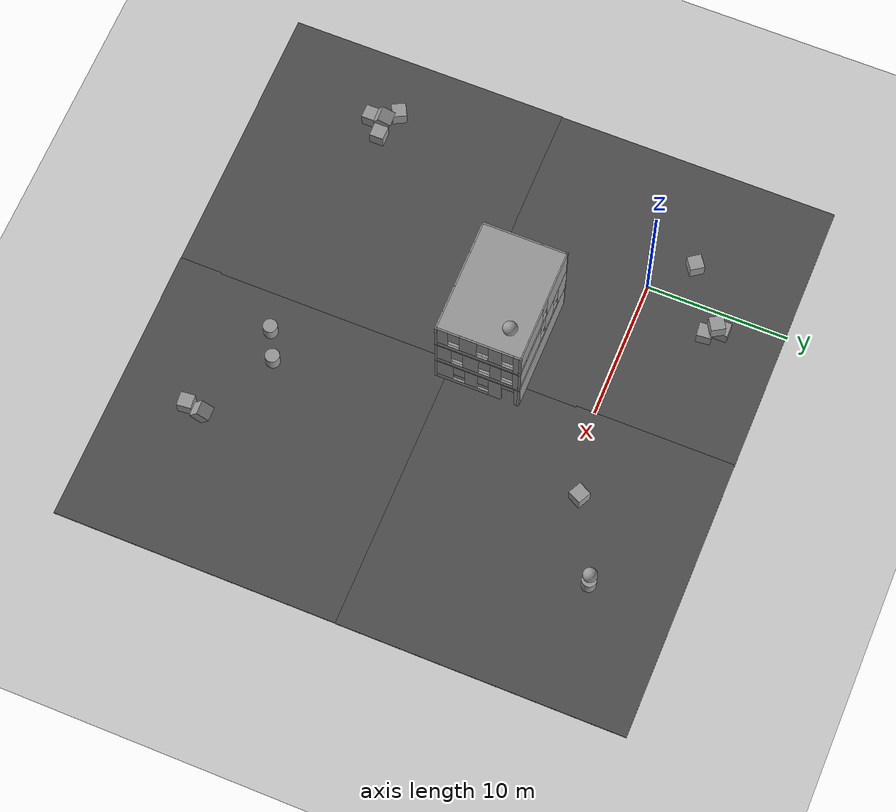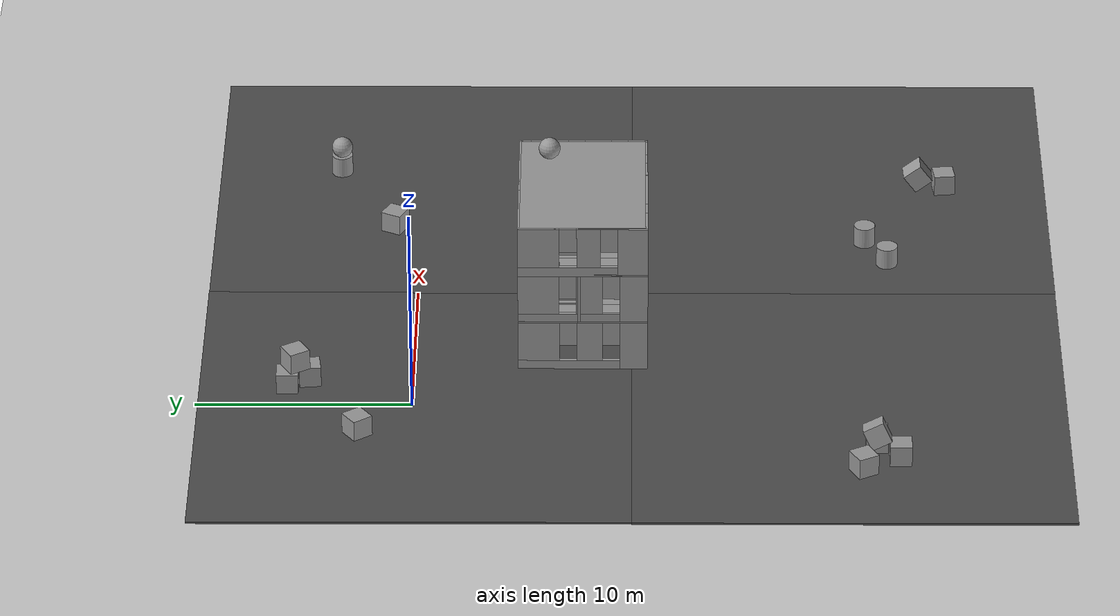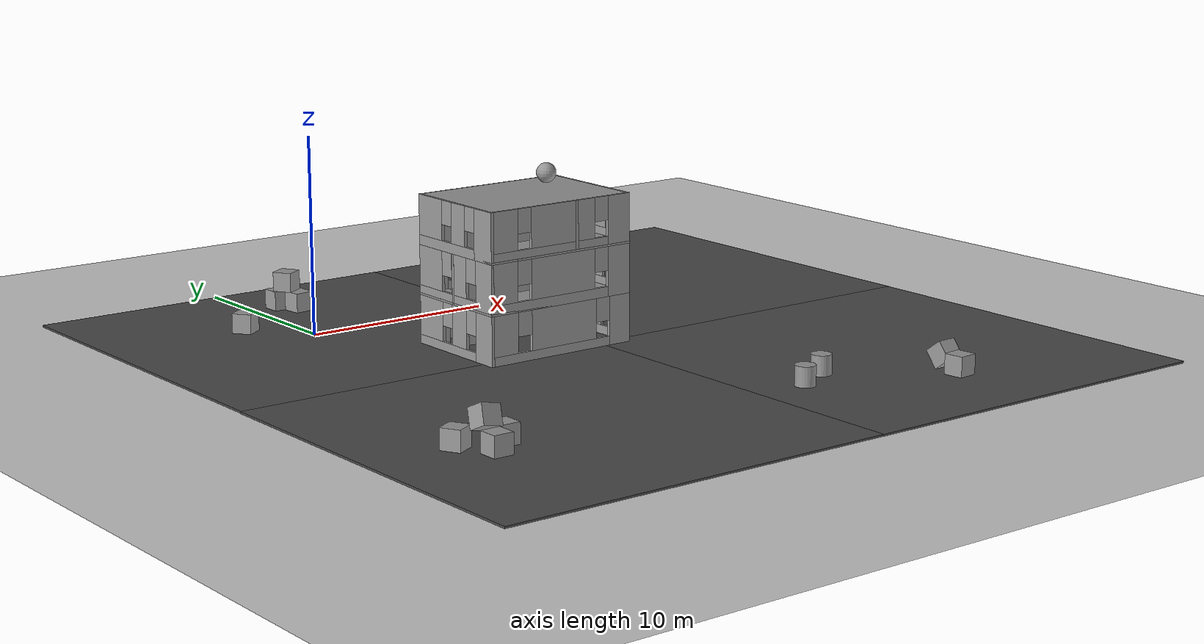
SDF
<sdf version="1.7">
 <world name="default">
  <plugin name="wavemap_ground_truth_plugin" filename="libwavemap_ground_truth_plugin.so"/>
  <light name="sun" type="directional">
   <pose>0 0 10 0 -0 0</pose>
   <diffuse>0.8 0.8 0.8 1</diffuse>
   <specular>0.1 0.1 0.1 1</specular>
   <attenuation>
    <range>1000</range>
    <constant>0.9</constant>
    <linear>0.01</linear>
    <quadratic>0.001</quadratic>
   </attenuation>
   <direction>-0.5 0.5 -1</direction>
   <spot><inner_angle>0</inner_angle><outer_angle>0</outer_angle><falloff>0</falloff></spot>
  </light>
  <model name="ground_plane">
   <static>1</static>
   <link name="link">
    <collision name="collision">
     <geometry><plane><normal>0 0 1</normal><size>100 100</size></plane></geometry>
     <surface><friction><ode><mu>100</mu><mu2>50</mu2></ode></friction></surface>
    </collision>
    <visual name="visual">
     <cast_shadows>0</cast_shadows>
     <geometry><plane><normal>0 0 1</normal><size>100 100</size></plane></geometry>
     <material>
      <script><uri>file://media/materials/scripts/gazebo.material</uri><name>Gazebo/Grey</name></script>
     </material>
    </visual>
   </link>
  </model>
  <gravity>0 0 -9.8</gravity>
  <magnetic_field>6e-06 2.3e-05 -4.2e-05</magnetic_field>
  <atmosphere type="adiabatic"/>
  <physics name="default_physics" default="0" type="ode">
   <max_step_size>0.001</max_step_size>
   <real_time_factor>1</real_time_factor>
   <real_time_update_rate>1000</real_time_update_rate>
  </physics>
  <scene><ambient>0.4 0.4 0.4 1</ambient><background>0.7 0.7 0.7 1</background><shadows>1</shadows></scene>
  <spherical_coordinates>
   <surface_model>EARTH_WGS84</surface_model>
   <latitude_deg>0</latitude_deg>
   <longitude_deg>0</longitude_deg>
   <elevation>0</elevation>
   <heading_deg>0</heading_deg>
  </spherical_coordinates>
  <model name="asphalt_plane">
   <static>1</static>
   <link name="link">
    <collision name="collision"><geometry><box><size>20 20 0.1</size></box></geometry></collision>
    <visual name="visual">
     <cast_shadows>0</cast_shadows>
     <geometry><box><size>20 20 0.1</size></box></geometry>
     <material>
      <script>
       <uri>model://asphalt_plane/materials/scripts</uri>
       <uri>model://asphalt_plane/materials/textures</uri>
       <name>vrc/asphalt</name>
      </script>
     </material>
    </visual>
   </link>
   <pose>0.058806 -0.094526 0 0 -0 0</pose>
  </model>
  <model name="asphalt_plane_0">
   <static>1</static>
   <link name="link">
    <collision name="collision"><geometry><box><size>20 20 0.1</size></box></geometry></collision>
    <visual name="visual">
     <cast_shadows>0</cast_shadows>
     <geometry><box><size>20 20 0.1</size></box></geometry>
     <material>
      <script>
       <uri>model://asphalt_plane/materials/scripts</uri>
       <uri>model://asphalt_plane/materials/textures</uri>
       <name>vrc/asphalt</name>
      </script>
     </material>
    </visual>
   </link>
   <pose>19.9513 -0.10756 0 0 -0 0</pose>
  </model>
  <model name="asphalt_plane_1">
   <static>1</static>
   <link name="link">
    <collision name="collision"><geometry><box><size>20 20 0.1</size></box></geometry></collision>
    <visual name="visual">
     <cast_shadows>0</cast_shadows>
     <geometry><box><size>20 20 0.1</size></box></geometry>
     <material>
      <script>
       <uri>model://asphalt_plane/materials/scripts</uri>
       <uri>model://asphalt_plane/materials/textures</uri>
       <name>vrc/asphalt</name>
      </script>
     </material>
    </visual>
   </link>
   <pose>0.022641 -20.0628 0 0 -0 0</pose>
  </model>
  <model name="asphalt_plane_2">
   <static>1</static>
   <link name="link">
    <collision name="collision"><geometry><box><size>20 20 0.1</size></box></geometry></collision>
    <visual name="visual">
     <cast_shadows>0</cast_shadows>
     <geometry><box><size>20 20 0.1</size></box></geometry>
     <material>
      <script>
       <uri>model://asphalt_plane/materials/scripts</uri>
       <uri>model://asphalt_plane/materials/textures</uri>
       <name>vrc/asphalt</name>
      </script>
     </material>
    </visual>
   </link>
   <pose>19.9368 -20.0754 0 0 -0 0</pose>
  </model>
  <model name="simple_building">
   <pose>7.31035 -7.81796 0 0 -0 0</pose>
   <link name="Floor_1">
    <pose>0 0.011464 2.5 0 -0 0</pose>
    <visual name="Floor_1_Visual_0">
     <pose>-3.37449 0 0.05 0 -0 0</pose>
     <geometry><box><size>1.54112 6 0.1</size></box></geometry>
     <material>
      <script><uri>file://media/materials/scripts/gazebo.material</uri><name>Gazebo/Grey</name></script>
      <ambient>1 1 1 1</ambient>
     </material>
    </visual>
    <collision name="Floor_1_Collision_0">
     <geometry><box><size>1.54112 6 0.1</size></box></geometry>
     <pose>-3.37449 0 0.05 0 -0 0</pose>
    </collision>
    <visual name="Floor_1_Visual_1">
     <pose>0.77056 -0.869196 0.05 0 -0 0</pose>
     <geometry><box><size>6.74898 4.26161 0.1</size></box></geometry>
     <material>
      <script><uri>file://media/materials/scripts/gazebo.material</uri><name>Gazebo/Grey</name></script>
      <ambient>1 1 1 1</ambient>
     </material>
    </visual>
    <collision name="Floor_1_Collision_1">
     <geometry><box><size>6.74898 4.26161 0.1</size></box></geometry>
     <pose>0.77056 -0.869196 0.05 0 -0 0</pose>
    </collision>
    <visual name="Floor_1_Visual_2">
     <pose>2.52056 2.1308 0.05 0 -0 0</pose>
     <geometry><box><size>3.24898 1.73839 0.1</size></box></geometry>
     <material>
      <script><uri>file://media/materials/scripts/gazebo.material</uri><name>Gazebo/Grey</name></script>
      <ambient>1 1 1 1</ambient>
     </material>
    </visual>
    <collision name="Floor_1_Collision_2">
     <geometry><box><size>3.24898 1.73839 0.1</size></box></geometry>
     <pose>2.52056 2.1308 0.05 0 -0 0</pose>
    </collision>
    <visual name="Floor_1_Visual_3">
     <pose>-0.85393 2.92738 0.05 0 -0 0</pose>
     <geometry><box><size>3.5 0.145251 0.1</size></box></geometry>
     <material>
      <script><uri>file://media/materials/scripts/gazebo.material</uri><name>Gazebo/Grey</name></script>
      <ambient>1 1 1 1</ambient>
     </material>
    </visual>
    <collision name="Floor_1_Collision_3">
     <geometry><box><size>3.5 0.145251 0.1</size></box></geometry>
     <pose>-0.85393 2.92738 0.05 0 -0 0</pose>
    </collision>
   </link>
   <link name="Floor_2">
    <pose>0.000567 0 5 0 -0 0</pose>
    <visual name="Floor_2_Visual_0">
     <pose>-3.37689 0 0.05 0 -0 0</pose>
     <geometry><box><size>1.53518 6.02293 0.1</size></box></geometry>
     <material>
      <script><uri>file://media/materials/scripts/gazebo.material</uri><name>Gazebo/Grey</name></script>
      <ambient>1 1 1 1</ambient>
     </material>
    </visual>
    <collision name="Floor_2_Collision_0">
     <geometry><box><size>1.53518 6.02293 0.1</size></box></geometry>
     <pose>-3.37689 0 0.05 0 -0 0</pose>
    </collision>
    <visual name="Floor_2_Visual_1">
     <pose>0.767592 -1.4216 0.05 0 -0 0</pose>
     <geometry><box><size>6.75378 3.17973 0.1</size></box></geometry>
     <material>
      <script><uri>file://media/materials/scripts/gazebo.material</uri><name>Gazebo/Grey</name></script>
      <ambient>1 1 1 1</ambient>
     </material>
    </visual>
    <collision name="Floor_2_Collision_1">
     <geometry><box><size>6.75378 3.17973 0.1</size></box></geometry>
     <pose>0.767592 -1.4216 0.05 0 -0 0</pose>
    </collision>
    <visual name="Floor_2_Visual_2">
     <pose>2.51759 1.58986 0.05 0 -0 0</pose>
     <geometry><box><size>3.25378 2.8432 0.1</size></box></geometry>
     <material>
      <script><uri>file://media/materials/scripts/gazebo.material</uri><name>Gazebo/Grey</name></script>
      <ambient>1 1 1 1</ambient>
     </material>
    </visual>
    <collision name="Floor_2_Collision_2">
     <geometry><box><size>3.25378 2.8432 0.1</size></box></geometry>
     <pose>2.51759 1.58986 0.05 0 -0 0</pose>
    </collision>
    <visual name="Floor_2_Visual_3">
     <pose>-0.859299 2.08986 0.05 0 -0 0</pose>
     <geometry><box><size>3.5 1.8432 0.1</size></box></geometry>
     <material>
      <script><uri>file://media/materials/scripts/gazebo.material</uri><name>Gazebo/Grey</name></script>
      <ambient>1 1 1 1</ambient>
     </material>
    </visual>
    <collision name="Floor_2_Collision_3">
     <geometry><box><size>3.5 1.8432 0.1</size></box></geometry>
     <pose>-0.859299 2.08986 0.05 0 -0 0</pose>
    </collision>
   </link>
   <link name="Stairs_0">
    <visual name="Stairs_0_Visual_0">
     <pose>0.779404 2.06964 0.083333 0 -0 -1.5708</pose>
     <geometry><box><size>1.59314 0.233333 0.166667</size></box></geometry>
     <material>
      <script><uri>file://media/materials/scripts/gazebo.material</uri><name>Gazebo/Grey</name></script>
      <ambient>1 1 1 1</ambient>
     </material>
    </visual>
    <collision name="Stairs_0_Collision_0">
     <geometry><box><size>1.59314 0.233333 0.166667</size></box></geometry>
     <pose>0.779404 2.06964 0.083333 0 -0 -1.5708</pose>
    </collision>
    <visual name="Stairs_0_Visual_1">
     <pose>0.54607 2.06964 0.25 0 -0 -1.5708</pose>
     <geometry><box><size>1.59314 0.233333 0.166667</size></box></geometry>
     <material>
      <script><uri>file://media/materials/scripts/gazebo.material</uri><name>Gazebo/Grey</name></script>
      <ambient>1 1 1 1</ambient>
     </material>
    </visual>
    <collision name="Stairs_0_Collision_1">
     <geometry><box><size>1.59314 0.233333 0.166667</size></box></geometry>
     <pose>0.54607 2.06964 0.25 0 -0 -1.5708</pose>
    </collision>
    <visual name="Stairs_0_Visual_2">
     <pose>0.312737 2.06964 0.416667 0 -0 -1.5708</pose>
     <geometry><box><size>1.59314 0.233333 0.166667</size></box></geometry>
     <material>
      <script><uri>file://media/materials/scripts/gazebo.material</uri><name>Gazebo/Grey</name></script>
      <ambient>1 1 1 1</ambient>
     </material>
    </visual>
    <collision name="Stairs_0_Collision_2">
     <geometry><box><size>1.59314 0.233333 0.166667</size></box></geometry>
     <pose>0.312737 2.06964 0.416667 0 -0 -1.5708</pose>
    </collision>
    <visual name="Stairs_0_Visual_3">
     <pose>0.079404 2.06964 0.583333 0 -0 -1.5708</pose>
     <geometry><box><size>1.59314 0.233333 0.166667</size></box></geometry>
     <material>
      <script><uri>file://media/materials/scripts/gazebo.material</uri><name>Gazebo/Grey</name></script>
      <ambient>1 1 1 1</ambient>
     </material>
    </visual>
    <collision name="Stairs_0_Collision_3">
     <geometry><box><size>1.59314 0.233333 0.166667</size></box></geometry>
     <pose>0.079404 2.06964 0.583333 0 -0 -1.5708</pose>
    </collision>
    <visual name="Stairs_0_Visual_4">
     <pose>-0.153929 2.06964 0.75 0 -0 -1.5708</pose>
     <geometry><box><size>1.59314 0.233333 0.166667</size></box></geometry>
     <material>
      <script><uri>file://media/materials/scripts/gazebo.material</uri><name>Gazebo/Grey</name></script>
      <ambient>1 1 1 1</ambient>
     </material>
    </visual>
    <collision name="Stairs_0_Collision_4">
     <geometry><box><size>1.59314 0.233333 0.166667</size></box></geometry>
     <pose>-0.153929 2.06964 0.75 0 -0 -1.5708</pose>
    </collision>
    <visual name="Stairs_0_Visual_5">
     <pose>-0.387263 2.06964 0.916667 0 -0 -1.5708</pose>
     <geometry><box><size>1.59314 0.233333 0.166667</size></box></geometry>
     <material>
      <script><uri>file://media/materials/scripts/gazebo.material</uri><name>Gazebo/Grey</name></script>
      <ambient>1 1 1 1</ambient>
     </material>
    </visual>
    <collision name="Stairs_0_Collision_5">
     <geometry><box><size>1.59314 0.233333 0.166667</size></box></geometry>
     <pose>-0.387263 2.06964 0.916667 0 -0 -1.5708</pose>
    </collision>
    <visual name="Stairs_0_Visual_6">
     <pose>-0.620596 2.06964 1.08333 0 -0 -1.5708</pose>
     <geometry><box><size>1.59314 0.233333 0.166667</size></box></geometry>
     <material>
      <script><uri>file://media/materials/scripts/gazebo.material</uri><name>Gazebo/Grey</name></script>
      <ambient>1 1 1 1</ambient>
     </material>
    </visual>
    <collision name="Stairs_0_Collision_6">
     <geometry><box><size>1.59314 0.233333 0.166667</size></box></geometry>
     <pose>-0.620596 2.06964 1.08333 0 -0 -1.5708</pose>
    </collision>
    <visual name="Stairs_0_Visual_7">
     <pose>-0.85393 2.06964 1.25 0 -0 -1.5708</pose>
     <geometry><box><size>1.59314 0.233333 0.166667</size></box></geometry>
     <material>
      <script><uri>file://media/materials/scripts/gazebo.material</uri><name>Gazebo/Grey</name></script>
      <ambient>1 1 1 1</ambient>
     </material>
    </visual>
    <collision name="Stairs_0_Collision_7">
     <geometry><box><size>1.59314 0.233333 0.166667</size></box></geometry>
     <pose>-0.85393 2.06964 1.25 0 -0 -1.5708</pose>
    </collision>
    <visual name="Stairs_0_Visual_8">
     <pose>-1.08726 2.06964 1.41667 0 -0 -1.5708</pose>
     <geometry><box><size>1.59314 0.233333 0.166667</size></box></geometry>
     <material>
      <script><uri>file://media/materials/scripts/gazebo.material</uri><name>Gazebo/Grey</name></script>
      <ambient>1 1 1 1</ambient>
     </material>
    </visual>
    <collision name="Stairs_0_Collision_8">
     <geometry><box><size>1.59314 0.233333 0.166667</size></box></geometry>
     <pose>-1.08726 2.06964 1.41667 0 -0 -1.5708</pose>
    </collision>
    <visual name="Stairs_0_Visual_9">
     <pose>-1.3206 2.06964 1.58333 0 -0 -1.5708</pose>
     <geometry><box><size>1.59314 0.233333 0.166667</size></box></geometry>
     <material>
      <script><uri>file://media/materials/scripts/gazebo.material</uri><name>Gazebo/Grey</name></script>
      <ambient>1 1 1 1</ambient>
     </material>
    </visual>
    <collision name="Stairs_0_Collision_9">
     <geometry><box><size>1.59314 0.233333 0.166667</size></box></geometry>
     <pose>-1.3206 2.06964 1.58333 0 -0 -1.5708</pose>
    </collision>
    <visual name="Stairs_0_Visual_10">
     <pose>-1.55393 2.06964 1.75 0 -0 -1.5708</pose>
     <geometry><box><size>1.59314 0.233333 0.166667</size></box></geometry>
     <material>
      <script><uri>file://media/materials/scripts/gazebo.material</uri><name>Gazebo/Grey</name></script>
      <ambient>1 1 1 1</ambient>
     </material>
    </visual>
    <collision name="Stairs_0_Collision_10">
     <geometry><box><size>1.59314 0.233333 0.166667</size></box></geometry>
     <pose>-1.55393 2.06964 1.75 0 -0 -1.5708</pose>
    </collision>
    <visual name="Stairs_0_Visual_11">
     <pose>-1.78726 2.06964 1.91667 0 -0 -1.5708</pose>
     <geometry><box><size>1.59314 0.233333 0.166667</size></box></geometry>
     <material>
      <script><uri>file://media/materials/scripts/gazebo.material</uri><name>Gazebo/Grey</name></script>
      <ambient>1 1 1 1</ambient>
     </material>
    </visual>
    <collision name="Stairs_0_Collision_11">
     <geometry><box><size>1.59314 0.233333 0.166667</size></box></geometry>
     <pose>-1.78726 2.06964 1.91667 0 -0 -1.5708</pose>
    </collision>
    <visual name="Stairs_0_Visual_12">
     <pose>-2.0206 2.06964 2.08333 0 -0 -1.5708</pose>
     <geometry><box><size>1.59314 0.233333 0.166667</size></box></geometry>
     <material>
      <script><uri>file://media/materials/scripts/gazebo.material</uri><name>Gazebo/Grey</name></script>
      <ambient>1 1 1 1</ambient>
     </material>
    </visual>
    <collision name="Stairs_0_Collision_12">
     <geometry><box><size>1.59314 0.233333 0.166667</size></box></geometry>
     <pose>-2.0206 2.06964 2.08333 0 -0 -1.5708</pose>
    </collision>
    <visual name="Stairs_0_Visual_13">
     <pose>-2.25393 2.06964 2.25 0 -0 -1.5708</pose>
     <geometry><box><size>1.59314 0.233333 0.166667</size></box></geometry>
     <material>
      <script><uri>file://media/materials/scripts/gazebo.material</uri><name>Gazebo/Grey</name></script>
      <ambient>1 1 1 1</ambient>
     </material>
    </visual>
    <collision name="Stairs_0_Collision_13">
     <geometry><box><size>1.59314 0.233333 0.166667</size></box></geometry>
     <pose>-2.25393 2.06964 2.25 0 -0 -1.5708</pose>
    </collision>
    <visual name="Stairs_0_Visual_14">
     <pose>-2.48726 2.06964 2.41667 0 -0 -1.5708</pose>
     <geometry><box><size>1.59314 0.233333 0.166667</size></box></geometry>
     <material>
      <script><uri>file://media/materials/scripts/gazebo.material</uri><name>Gazebo/Grey</name></script>
      <ambient>1 1 1 1</ambient>
     </material>
    </visual>
    <collision name="Stairs_0_Collision_14">
     <geometry><box><size>1.59314 0.233333 0.166667</size></box></geometry>
     <pose>-2.48726 2.06964 2.41667 0 -0 -1.5708</pose>
    </collision>
   </link>
   <link name="Stairs_3">
    <visual name="Stairs_3_Visual_0">
     <pose>-2.49207 0.668263 2.58333 0 -0 1.5708</pose>
     <geometry><box><size>1 0.233333 0.166667</size></box></geometry>
     <material>
      <script><uri>file://media/materials/scripts/gazebo.material</uri><name>Gazebo/Grey</name></script>
      <ambient>1 1 1 1</ambient>
     </material>
    </visual>
    <collision name="Stairs_3_Collision_0">
     <geometry><box><size>1 0.233333 0.166667</size></box></geometry>
     <pose>-2.49207 0.668263 2.58333 0 -0 1.5708</pose>
    </collision>
    <visual name="Stairs_3_Visual_1">
     <pose>-2.25873 0.668263 2.75 0 -0 1.5708</pose>
     <geometry><box><size>1 0.233333 0.166667</size></box></geometry>
     <material>
      <script><uri>file://media/materials/scripts/gazebo.material</uri><name>Gazebo/Grey</name></script>
      <ambient>1 1 1 1</ambient>
     </material>
    </visual>
    <collision name="Stairs_3_Collision_1">
     <geometry><box><size>1 0.233333 0.166667</size></box></geometry>
     <pose>-2.25873 0.668263 2.75 0 -0 1.5708</pose>
    </collision>
    <visual name="Stairs_3_Visual_2">
     <pose>-2.0254 0.668263 2.91667 0 -0 1.5708</pose>
     <geometry><box><size>1 0.233333 0.166667</size></box></geometry>
     <material>
      <script><uri>file://media/materials/scripts/gazebo.material</uri><name>Gazebo/Grey</name></script>
      <ambient>1 1 1 1</ambient>
     </material>
    </visual>
    <collision name="Stairs_3_Collision_2">
     <geometry><box><size>1 0.233333 0.166667</size></box></geometry>
     <pose>-2.0254 0.668263 2.91667 0 -0 1.5708</pose>
    </collision>
    <visual name="Stairs_3_Visual_3">
     <pose>-1.79207 0.668263 3.08333 0 -0 1.5708</pose>
     <geometry><box><size>1 0.233333 0.166667</size></box></geometry>
     <material>
      <script><uri>file://media/materials/scripts/gazebo.material</uri><name>Gazebo/Grey</name></script>
      <ambient>1 1 1 1</ambient>
     </material>
    </visual>
    <collision name="Stairs_3_Collision_3">
     <geometry><box><size>1 0.233333 0.166667</size></box></geometry>
     <pose>-1.79207 0.668263 3.08333 0 -0 1.5708</pose>
    </collision>
    <visual name="Stairs_3_Visual_4">
     <pose>-1.55873 0.668264 3.25 0 -0 1.5708</pose>
     <geometry><box><size>1 0.233333 0.166667</size></box></geometry>
     <material>
      <script><uri>file://media/materials/scripts/gazebo.material</uri><name>Gazebo/Grey</name></script>
      <ambient>1 1 1 1</ambient>
     </material>
    </visual>
    <collision name="Stairs_3_Collision_4">
     <geometry><box><size>1 0.233333 0.166667</size></box></geometry>
     <pose>-1.55873 0.668264 3.25 0 -0 1.5708</pose>
    </collision>
    <visual name="Stairs_3_Visual_5">
     <pose>-1.3254 0.668264 3.41667 0 -0 1.5708</pose>
     <geometry><box><size>1 0.233333 0.166667</size></box></geometry>
     <material>
      <script><uri>file://media/materials/scripts/gazebo.material</uri><name>Gazebo/Grey</name></script>
      <ambient>1 1 1 1</ambient>
     </material>
    </visual>
    <collision name="Stairs_3_Collision_5">
     <geometry><box><size>1 0.233333 0.166667</size></box></geometry>
     <pose>-1.3254 0.668264 3.41667 0 -0 1.5708</pose>
    </collision>
    <visual name="Stairs_3_Visual_6">
     <pose>-1.09207 0.668264 3.58333 0 -0 1.5708</pose>
     <geometry><box><size>1 0.233333 0.166667</size></box></geometry>
     <material>
      <script><uri>file://media/materials/scripts/gazebo.material</uri><name>Gazebo/Grey</name></script>
      <ambient>1 1 1 1</ambient>
     </material>
    </visual>
    <collision name="Stairs_3_Collision_6">
     <geometry><box><size>1 0.233333 0.166667</size></box></geometry>
     <pose>-1.09207 0.668264 3.58333 0 -0 1.5708</pose>
    </collision>
    <visual name="Stairs_3_Visual_7">
     <pose>-0.858732 0.668264 3.75 0 -0 1.5708</pose>
     <geometry><box><size>1 0.233333 0.166667</size></box></geometry>
     <material>
      <script><uri>file://media/materials/scripts/gazebo.material</uri><name>Gazebo/Grey</name></script>
      <ambient>1 1 1 1</ambient>
     </material>
    </visual>
    <collision name="Stairs_3_Collision_7">
     <geometry><box><size>1 0.233333 0.166667</size></box></geometry>
     <pose>-0.858732 0.668264 3.75 0 -0 1.5708</pose>
    </collision>
    <visual name="Stairs_3_Visual_8">
     <pose>-0.625398 0.668264 3.91667 0 -0 1.5708</pose>
     <geometry><box><size>1 0.233333 0.166667</size></box></geometry>
     <material>
      <script><uri>file://media/materials/scripts/gazebo.material</uri><name>Gazebo/Grey</name></script>
      <ambient>1 1 1 1</ambient>
     </material>
    </visual>
    <collision name="Stairs_3_Collision_8">
     <geometry><box><size>1 0.233333 0.166667</size></box></geometry>
     <pose>-0.625398 0.668264 3.91667 0 -0 1.5708</pose>
    </collision>
    <visual name="Stairs_3_Visual_9">
     <pose>-0.392065 0.668264 4.08333 0 -0 1.5708</pose>
     <geometry><box><size>1 0.233333 0.166667</size></box></geometry>
     <material>
      <script><uri>file://media/materials/scripts/gazebo.material</uri><name>Gazebo/Grey</name></script>
      <ambient>1 1 1 1</ambient>
     </material>
    </visual>
    <collision name="Stairs_3_Collision_9">
     <geometry><box><size>1 0.233333 0.166667</size></box></geometry>
     <pose>-0.392065 0.668264 4.08333 0 -0 1.5708</pose>
    </collision>
    <visual name="Stairs_3_Visual_10">
     <pose>-0.158731 0.668264 4.25 0 -0 1.5708</pose>
     <geometry><box><size>1 0.233333 0.166667</size></box></geometry>
     <material>
      <script><uri>file://media/materials/scripts/gazebo.material</uri><name>Gazebo/Grey</name></script>
      <ambient>1 1 1 1</ambient>
     </material>
    </visual>
    <collision name="Stairs_3_Collision_10">
     <geometry><box><size>1 0.233333 0.166667</size></box></geometry>
     <pose>-0.158731 0.668264 4.25 0 -0 1.5708</pose>
    </collision>
    <visual name="Stairs_3_Visual_11">
     <pose>0.074602 0.668264 4.41667 0 -0 1.5708</pose>
     <geometry><box><size>1 0.233333 0.166667</size></box></geometry>
     <material>
      <script><uri>file://media/materials/scripts/gazebo.material</uri><name>Gazebo/Grey</name></script>
      <ambient>1 1 1 1</ambient>
     </material>
    </visual>
    <collision name="Stairs_3_Collision_11">
     <geometry><box><size>1 0.233333 0.166667</size></box></geometry>
     <pose>0.074602 0.668264 4.41667 0 -0 1.5708</pose>
    </collision>
    <visual name="Stairs_3_Visual_12">
     <pose>0.307935 0.668264 4.58333 0 -0 1.5708</pose>
     <geometry><box><size>1 0.233333 0.166667</size></box></geometry>
     <material>
      <script><uri>file://media/materials/scripts/gazebo.material</uri><name>Gazebo/Grey</name></script>
      <ambient>1 1 1 1</ambient>
     </material>
    </visual>
    <collision name="Stairs_3_Collision_12">
     <geometry><box><size>1 0.233333 0.166667</size></box></geometry>
     <pose>0.307935 0.668264 4.58333 0 -0 1.5708</pose>
    </collision>
    <visual name="Stairs_3_Visual_13">
     <pose>0.541269 0.668264 4.75 0 -0 1.5708</pose>
     <geometry><box><size>1 0.233333 0.166667</size></box></geometry>
     <material>
      <script><uri>file://media/materials/scripts/gazebo.material</uri><name>Gazebo/Grey</name></script>
      <ambient>1 1 1 1</ambient>
     </material>
    </visual>
    <collision name="Stairs_3_Collision_13">
     <geometry><box><size>1 0.233333 0.166667</size></box></geometry>
     <pose>0.541269 0.668264 4.75 0 -0 1.5708</pose>
    </collision>
    <visual name="Stairs_3_Visual_14">
     <pose>0.774602 0.668264 4.91667 0 -0 1.5708</pose>
     <geometry><box><size>1 0.233333 0.166667</size></box></geometry>
     <material>
      <script><uri>file://media/materials/scripts/gazebo.material</uri><name>Gazebo/Grey</name></script>
      <ambient>1 1 1 1</ambient>
     </material>
    </visual>
    <collision name="Stairs_3_Collision_14">
     <geometry><box><size>1 0.233333 0.166667</size></box></geometry>
     <pose>0.774602 0.668264 4.91667 0 -0 1.5708</pose>
    </collision>
   </link>
   <link name="Wall_1">
    <pose>-4.06892 0.011464 0 0 -0 1.5708</pose>
    <visual name="Wall_1_Visual_0">
     <pose>-2.34908 0 1.25 0 -0 0</pose>
     <geometry><box><size>1.30184 0.15 2.5</size></box></geometry>
     <material>
      <script><uri>file://media/materials/scripts/gazebo.material</uri><name>Gazebo/Grey</name></script>
      <ambient>1 1 1 1</ambient>
     </material>
    </visual>
    <collision name="Wall_1_Collision_0">
     <geometry><box><size>1.30184 0.15 2.5</size></box></geometry>
     <pose>-2.34908 0 1.25 0 -0 0</pose>
    </collision>
    <visual name="Wall_1_Visual_1">
     <pose>0.650921 0 0.25 0 -0 0</pose>
     <geometry><box><size>4.69816 0.15 0.5</size></box></geometry>
     <material>
      <script><uri>file://media/materials/scripts/gazebo.material</uri><name>Gazebo/Grey</name></script>
      <ambient>1 1 1 1</ambient>
     </material>
    </visual>
    <collision name="Wall_1_Collision_1">
     <geometry><box><size>4.69816 0.15 0.5</size></box></geometry>
     <pose>0.650921 0 0.25 0 -0 0</pose>
    </collision>
    <visual name="Wall_1_Visual_2">
     <pose>-0.309589 0 1.5 0 -0 0</pose>
     <geometry><box><size>1.17714 0.15 2</size></box></geometry>
     <material>
      <script><uri>file://media/materials/scripts/gazebo.material</uri><name>Gazebo/Grey</name></script>
      <ambient>1 1 1 1</ambient>
     </material>
    </visual>
    <collision name="Wall_1_Collision_2">
     <geometry><box><size>1.17714 0.15 2</size></box></geometry>
     <pose>-0.309589 0 1.5 0 -0 0</pose>
    </collision>
    <visual name="Wall_1_Visual_3">
     <pose>2.03949 0 1.5 0 -0 0</pose>
     <geometry><box><size>1.92102 0.15 2</size></box></geometry>
     <material>
      <script><uri>file://media/materials/scripts/gazebo.material</uri><name>Gazebo/Grey</name></script>
      <ambient>1 1 1 1</ambient>
     </material>
    </visual>
    <collision name="Wall_1_Collision_3">
     <geometry><box><size>1.92102 0.15 2</size></box></geometry>
     <pose>2.03949 0 1.5 0 -0 0</pose>
    </collision>
    <visual name="Wall_1_Visual_4">
     <pose>-1.29816 0 1.9 0 -0 0</pose>
     <geometry><box><size>0.8 0.15 1.2</size></box></geometry>
     <material>
      <script><uri>file://media/materials/scripts/gazebo.material</uri><name>Gazebo/Grey</name></script>
      <ambient>1 1 1 1</ambient>
     </material>
    </visual>
    <collision name="Wall_1_Collision_4">
     <geometry><box><size>0.8 0.15 1.2</size></box></geometry>
     <pose>-1.29816 0 1.9 0 -0 0</pose>
    </collision>
    <visual name="Wall_1_Visual_5">
     <pose>0.678979 0 1.9 0 -0 0</pose>
     <geometry><box><size>0.8 0.15 1.2</size></box></geometry>
     <material>
      <script><uri>file://media/materials/scripts/gazebo.material</uri><name>Gazebo/Grey</name></script>
      <ambient>1 1 1 1</ambient>
     </material>
    </visual>
    <collision name="Wall_1_Collision_5">
     <geometry><box><size>0.8 0.15 1.2</size></box></geometry>
     <pose>0.678979 0 1.9 0 -0 0</pose>
    </collision>
   </link>
   <link name="Wall_10">
    <pose>-1.60572 1.23127 0 0 -0 3.14159</pose>
    <visual name="Wall_10_Visual_0">
     <pose>-0.661074 0 1.25 0 -0 0</pose>
     <geometry><box><size>3.67785 0.15 2.5</size></box></geometry>
     <material>
      <script><uri>file://media/materials/scripts/gazebo.material</uri><name>Gazebo/Grey</name></script>
      <ambient>1 1 1 1</ambient>
     </material>
    </visual>
    <collision name="Wall_10_Collision_0">
     <geometry><box><size>3.67785 0.15 2.5</size></box></geometry>
     <pose>-0.661074 0 1.25 0 -0 0</pose>
    </collision>
    <visual name="Wall_10_Visual_1">
     <pose>2.28893 0 1.25 0 -0 0</pose>
     <geometry><box><size>0.422147 0.15 2.5</size></box></geometry>
     <material>
      <script><uri>file://media/materials/scripts/gazebo.material</uri><name>Gazebo/Grey</name></script>
      <ambient>1 1 1 1</ambient>
     </material>
    </visual>
    <collision name="Wall_10_Collision_1">
     <geometry><box><size>0.422147 0.15 2.5</size></box></geometry>
     <pose>2.28893 0 1.25 0 -0 0</pose>
    </collision>
    <visual name="Wall_10_Visual_2">
     <pose>1.62785 0 2.25 0 -0 0</pose>
     <geometry><box><size>0.9 0.15 0.5</size></box></geometry>
     <material>
      <script><uri>file://media/materials/scripts/gazebo.material</uri><name>Gazebo/Grey</name></script>
      <ambient>1 1 1 1</ambient>
     </material>
    </visual>
    <collision name="Wall_10_Collision_2">
     <geometry><box><size>0.9 0.15 0.5</size></box></geometry>
     <pose>1.62785 0 2.25 0 -0 0</pose>
    </collision>
   </link>
   <link name="Wall_17">
    <pose>-4.06892 0.011464 2.5 0 -0 1.5708</pose>
    <visual name="Wall_17_Visual_0">
     <pose>-2.35668 0 1.25 0 -0 0</pose>
     <geometry><box><size>1.28663 0.15 2.5</size></box></geometry>
     <material>
      <script><uri>file://media/materials/scripts/gazebo.material</uri><name>Gazebo/Grey</name></script>
      <ambient>1 1 1 1</ambient>
     </material>
    </visual>
    <collision name="Wall_17_Collision_0">
     <geometry><box><size>1.28663 0.15 2.5</size></box></geometry>
     <pose>-2.35668 0 1.25 0 -0 0</pose>
    </collision>
    <visual name="Wall_17_Visual_1">
     <pose>0.643317 0 0.25 0 -0 0</pose>
     <geometry><box><size>4.71337 0.15 0.5</size></box></geometry>
     <material>
      <script><uri>file://media/materials/scripts/gazebo.material</uri><name>Gazebo/Grey</name></script>
      <ambient>1 1 1 1</ambient>
     </material>
    </visual>
    <collision name="Wall_17_Collision_1">
     <geometry><box><size>4.71337 0.15 0.5</size></box></geometry>
     <pose>0.643317 0 0.25 0 -0 0</pose>
    </collision>
    <visual name="Wall_17_Visual_2">
     <pose>-0.309589 0 1.5 0 -0 0</pose>
     <geometry><box><size>1.20755 0.15 2</size></box></geometry>
     <material>
      <script><uri>file://media/materials/scripts/gazebo.material</uri><name>Gazebo/Grey</name></script>
      <ambient>1 1 1 1</ambient>
     </material>
    </visual>
    <collision name="Wall_17_Collision_2">
     <geometry><box><size>1.20755 0.15 2</size></box></geometry>
     <pose>-0.309589 0 1.5 0 -0 0</pose>
    </collision>
    <visual name="Wall_17_Visual_3">
     <pose>2.04709 0 1.5 0 -0 0</pose>
     <geometry><box><size>1.90581 0.15 2</size></box></geometry>
     <material>
      <script><uri>file://media/materials/scripts/gazebo.material</uri><name>Gazebo/Grey</name></script>
      <ambient>1 1 1 1</ambient>
     </material>
    </visual>
    <collision name="Wall_17_Collision_3">
     <geometry><box><size>1.90581 0.15 2</size></box></geometry>
     <pose>2.04709 0 1.5 0 -0 0</pose>
    </collision>
    <visual name="Wall_17_Visual_4">
     <pose>-1.31337 0 1.9 0 -0 0</pose>
     <geometry><box><size>0.8 0.15 1.2</size></box></geometry>
     <material>
      <script><uri>file://media/materials/scripts/gazebo.material</uri><name>Gazebo/Grey</name></script>
      <ambient>1 1 1 1</ambient>
     </material>
    </visual>
    <collision name="Wall_17_Collision_4">
     <geometry><box><size>0.8 0.15 1.2</size></box></geometry>
     <pose>-1.31337 0 1.9 0 -0 0</pose>
    </collision>
    <visual name="Wall_17_Visual_5">
     <pose>0.694188 0 1.9 0 -0 0</pose>
     <geometry><box><size>0.8 0.15 1.2</size></box></geometry>
     <material>
      <script><uri>file://media/materials/scripts/gazebo.material</uri><name>Gazebo/Grey</name></script>
      <ambient>1 1 1 1</ambient>
     </material>
    </visual>
    <collision name="Wall_17_Collision_5">
     <geometry><box><size>0.8 0.15 1.2</size></box></geometry>
     <pose>0.694188 0 1.9 0 -0 0</pose>
    </collision>
   </link>
   <link name="Wall_18">
    <pose>0.008172 2.93646 2.5 0 -0 0</pose>
    <visual name="Wall_18_Visual_0">
     <pose>-3.37982 0 1.25 0 -0 0</pose>
     <geometry><box><size>1.51412 0.15 2.5</size></box></geometry>
     <material>
      <script><uri>file://media/materials/scripts/gazebo.material</uri><name>Gazebo/Grey</name></script>
      <ambient>1 1 1 1</ambient>
     </material>
    </visual>
    <collision name="Wall_18_Collision_0">
     <geometry><box><size>1.51412 0.15 2.5</size></box></geometry>
     <pose>-3.37982 0 1.25 0 -0 0</pose>
    </collision>
    <visual name="Wall_18_Visual_1">
     <pose>0.757062 0 0.25 0 -0 0</pose>
     <geometry><box><size>6.75963 0.15 0.5</size></box></geometry>
     <material>
      <script><uri>file://media/materials/scripts/gazebo.material</uri><name>Gazebo/Grey</name></script>
      <ambient>1 1 1 1</ambient>
     </material>
    </visual>
    <collision name="Wall_18_Collision_1">
     <geometry><box><size>6.75963 0.15 0.5</size></box></geometry>
     <pose>0.757062 0 0.25 0 -0 0</pose>
    </collision>
    <visual name="Wall_18_Visual_2">
     <pose>-1.0897 0 1.5 0 -0 0</pose>
     <geometry><box><size>1.4661 0.15 2</size></box></geometry>
     <material>
      <script><uri>file://media/materials/scripts/gazebo.material</uri><name>Gazebo/Grey</name></script>
      <ambient>1 1 1 1</ambient>
     </material>
    </visual>
    <collision name="Wall_18_Collision_2">
     <geometry><box><size>1.4661 0.15 2</size></box></geometry>
     <pose>-1.0897 0 1.5 0 -0 0</pose>
    </collision>
    <visual name="Wall_18_Visual_3">
     <pose>2.29011 0 1.5 0 -0 0</pose>
     <geometry><box><size>3.69353 0.15 2</size></box></geometry>
     <material>
      <script><uri>file://media/materials/scripts/gazebo.material</uri><name>Gazebo/Grey</name></script>
      <ambient>1 1 1 1</ambient>
     </material>
    </visual>
    <collision name="Wall_18_Collision_3">
     <geometry><box><size>3.69353 0.15 2</size></box></geometry>
     <pose>2.29011 0 1.5 0 -0 0</pose>
    </collision>
    <visual name="Wall_18_Visual_4">
     <pose>-2.22275 0 1.9 0 -0 0</pose>
     <geometry><box><size>0.8 0.15 1.2</size></box></geometry>
     <material>
      <script><uri>file://media/materials/scripts/gazebo.material</uri><name>Gazebo/Grey</name></script>
      <ambient>1 1 1 1</ambient>
     </material>
    </visual>
    <collision name="Wall_18_Collision_4">
     <geometry><box><size>0.8 0.15 1.2</size></box></geometry>
     <pose>-2.22275 0 1.9 0 -0 0</pose>
    </collision>
    <visual name="Wall_18_Visual_5">
     <pose>0.043349 0 1.9 0 -0 0</pose>
     <geometry><box><size>0.8 0.15 1.2</size></box></geometry>
     <material>
      <script><uri>file://media/materials/scripts/gazebo.material</uri><name>Gazebo/Grey</name></script>
      <ambient>1 1 1 1</ambient>
     </material>
    </visual>
    <collision name="Wall_18_Collision_5">
     <geometry><box><size>0.8 0.15 1.2</size></box></geometry>
     <pose>0.043349 0 1.9 0 -0 0</pose>
    </collision>
   </link>
   <link name="Wall_19">
    <pose>4.05484 0.011464 2.5 0 0 -1.5708</pose>
    <visual name="Wall_19_Visual_0">
     <pose>-2.73149 0 1.25 0 -0 0</pose>
     <geometry><box><size>0.537024 0.15 2.5</size></box></geometry>
     <material>
      <script><uri>file://media/materials/scripts/gazebo.material</uri><name>Gazebo/Grey</name></script>
      <ambient>1 1 1 1</ambient>
     </material>
    </visual>
    <collision name="Wall_19_Collision_0">
     <geometry><box><size>0.537024 0.15 2.5</size></box></geometry>
     <pose>-2.73149 0 1.25 0 -0 0</pose>
    </collision>
    <visual name="Wall_19_Visual_1">
     <pose>0.268512 0 0.25 0 -0 0</pose>
     <geometry><box><size>5.46298 0.15 0.5</size></box></geometry>
     <material>
      <script><uri>file://media/materials/scripts/gazebo.material</uri><name>Gazebo/Grey</name></script>
      <ambient>1 1 1 1</ambient>
     </material>
    </visual>
    <collision name="Wall_19_Collision_1">
     <geometry><box><size>5.46298 0.15 0.5</size></box></geometry>
     <pose>0.268512 0 0.25 0 -0 0</pose>
    </collision>
    <visual name="Wall_19_Visual_2">
     <pose>-1.27212 0 1.5 0 -0 0</pose>
     <geometry><box><size>0.78171 0.15 2</size></box></geometry>
     <material>
      <script><uri>file://media/materials/scripts/gazebo.material</uri><name>Gazebo/Grey</name></script>
      <ambient>1 1 1 1</ambient>
     </material>
    </visual>
    <collision name="Wall_19_Collision_2">
     <geometry><box><size>0.78171 0.15 2</size></box></geometry>
     <pose>-1.27212 0 1.5 0 -0 0</pose>
    </collision>
    <visual name="Wall_19_Visual_3">
     <pose>0.469281 0 1.5 0 -0 0</pose>
     <geometry><box><size>1.10109 0.15 2</size></box></geometry>
     <material>
      <script><uri>file://media/materials/scripts/gazebo.material</uri><name>Gazebo/Grey</name></script>
      <ambient>1 1 1 1</ambient>
     </material>
    </visual>
    <collision name="Wall_19_Collision_3">
     <geometry><box><size>1.10109 0.15 2</size></box></geometry>
     <pose>0.469281 0 1.5 0 -0 0</pose>
    </collision>
    <visual name="Wall_19_Visual_4">
     <pose>2.40991 0 1.5 0 -0 0</pose>
     <geometry><box><size>1.18017 0.15 2</size></box></geometry>
     <material>
      <script><uri>file://media/materials/scripts/gazebo.material</uri><name>Gazebo/Grey</name></script>
      <ambient>1 1 1 1</ambient>
     </material>
    </visual>
    <collision name="Wall_19_Collision_4">
     <geometry><box><size>1.18017 0.15 2</size></box></geometry>
     <pose>2.40991 0 1.5 0 -0 0</pose>
    </collision>
    <visual name="Wall_19_Visual_5">
     <pose>-2.06298 0 1.9 0 -0 0</pose>
     <geometry><box><size>0.8 0.15 1.2</size></box></geometry>
     <material>
      <script><uri>file://media/materials/scripts/gazebo.material</uri><name>Gazebo/Grey</name></script>
      <ambient>1 1 1 1</ambient>
     </material>
    </visual>
    <collision name="Wall_19_Collision_5">
     <geometry><box><size>0.8 0.15 1.2</size></box></geometry>
     <pose>-2.06298 0 1.9 0 -0 0</pose>
    </collision>
    <visual name="Wall_19_Visual_6">
     <pose>-0.481266 0 1.9 0 -0 0</pose>
     <geometry><box><size>0.8 0.15 1.2</size></box></geometry>
     <material>
      <script><uri>file://media/materials/scripts/gazebo.material</uri><name>Gazebo/Grey</name></script>
      <ambient>1 1 1 1</ambient>
     </material>
    </visual>
    <collision name="Wall_19_Collision_6">
     <geometry><box><size>0.8 0.15 1.2</size></box></geometry>
     <pose>-0.481266 0 1.9 0 -0 0</pose>
    </collision>
    <visual name="Wall_19_Visual_7">
     <pose>1.41983 0 1.9 0 -0 0</pose>
     <geometry><box><size>0.8 0.15 1.2</size></box></geometry>
     <material>
      <script><uri>file://media/materials/scripts/gazebo.material</uri><name>Gazebo/Grey</name></script>
      <ambient>1 1 1 1</ambient>
     </material>
    </visual>
    <collision name="Wall_19_Collision_7">
     <geometry><box><size>0.8 0.15 1.2</size></box></geometry>
     <pose>1.41983 0 1.9 0 -0 0</pose>
    </collision>
   </link>
   <link name="Wall_2">
    <collision name="Wall_2_Collision">
     <geometry><box><size>8.27376 0.15 2.5</size></box></geometry>
     <pose>0 0 1.25 0 -0 0</pose>
    </collision>
    <visual name="Wall_2_Visual">
     <pose>0 0 1.25 0 -0 0</pose>
     <geometry><box><size>8.27376 0.15 2.5</size></box></geometry>
     <material>
      <script><uri>file://media/materials/scripts/gazebo.material</uri><name>Gazebo/Grey</name></script>
      <ambient>1 1 1 1</ambient>
     </material>
    </visual>
    <pose>0.008172 2.93646 0 0 -0 0</pose>
   </link>
   <link name="Wall_20">
    <pose>0.008172 -2.91354 2.5 0 -0 3.14159</pose>
    <visual name="Wall_20_Visual_0">
     <pose>-3.46119 0 1.25 0 -0 0</pose>
     <geometry><box><size>1.35138 0.15 2.5</size></box></geometry>
     <material>
      <script><uri>file://media/materials/scripts/gazebo.material</uri><name>Gazebo/Grey</name></script>
      <ambient>1 1 1 1</ambient>
     </material>
    </visual>
    <collision name="Wall_20_Collision_0">
     <geometry><box><size>1.35138 0.15 2.5</size></box></geometry>
     <pose>-3.46119 0 1.25 0 -0 0</pose>
    </collision>
    <visual name="Wall_20_Visual_1">
     <pose>0.675691 0 0.25 0 -0 0</pose>
     <geometry><box><size>6.92237 0.15 0.5</size></box></geometry>
     <material>
      <script><uri>file://media/materials/scripts/gazebo.material</uri><name>Gazebo/Grey</name></script>
      <ambient>1 1 1 1</ambient>
     </material>
    </visual>
    <collision name="Wall_20_Collision_1">
     <geometry><box><size>6.92237 0.15 0.5</size></box></geometry>
     <pose>0.675691 0 0.25 0 -0 0</pose>
    </collision>
    <visual name="Wall_20_Visual_2">
     <pose>-0.088975 0 1.5 0 -0 0</pose>
     <geometry><box><size>3.79304 0.15 2</size></box></geometry>
     <material>
      <script><uri>file://media/materials/scripts/gazebo.material</uri><name>Gazebo/Grey</name></script>
      <ambient>1 1 1 1</ambient>
     </material>
    </visual>
    <collision name="Wall_20_Collision_2">
     <geometry><box><size>3.79304 0.15 2</size></box></geometry>
     <pose>-0.088975 0 1.5 0 -0 0</pose>
    </collision>
    <visual name="Wall_20_Visual_3">
     <pose>3.37221 0 1.5 0 -0 0</pose>
     <geometry><box><size>1.52933 0.15 2</size></box></geometry>
     <material>
      <script><uri>file://media/materials/scripts/gazebo.material</uri><name>Gazebo/Grey</name></script>
      <ambient>1 1 1 1</ambient>
     </material>
    </visual>
    <collision name="Wall_20_Collision_3">
     <geometry><box><size>1.52933 0.15 2</size></box></geometry>
     <pose>3.37221 0 1.5 0 -0 0</pose>
    </collision>
    <visual name="Wall_20_Visual_4">
     <pose>-2.3855 0 1.9 0 -0 0</pose>
     <geometry><box><size>0.8 0.15 1.2</size></box></geometry>
     <material>
      <script><uri>file://media/materials/scripts/gazebo.material</uri><name>Gazebo/Grey</name></script>
      <ambient>1 1 1 1</ambient>
     </material>
    </visual>
    <collision name="Wall_20_Collision_4">
     <geometry><box><size>0.8 0.15 1.2</size></box></geometry>
     <pose>-2.3855 0 1.9 0 -0 0</pose>
    </collision>
    <visual name="Wall_20_Visual_5">
     <pose>2.20755 0 1.9 0 -0 0</pose>
     <geometry><box><size>0.8 0.15 1.2</size></box></geometry>
     <material>
      <script><uri>file://media/materials/scripts/gazebo.material</uri><name>Gazebo/Grey</name></script>
      <ambient>1 1 1 1</ambient>
     </material>
    </visual>
    <collision name="Wall_20_Collision_5">
     <geometry><box><size>0.8 0.15 1.2</size></box></geometry>
     <pose>2.20755 0 1.9 0 -0 0</pose>
    </collision>
   </link>
   <link name="Wall_21">
    <collision name="Wall_21_Collision">
     <geometry><box><size>3.5 0.15 2.5</size></box></geometry>
     <pose>0 0 1.25 0 -0 0</pose>
    </collision>
    <visual name="Wall_21_Visual">
     <pose>0 0 1.25 0 -0 0</pose>
     <geometry><box><size>3.5 0.15 2.5</size></box></geometry>
     <material>
      <script><uri>file://media/materials/scripts/gazebo.material</uri><name>Gazebo/Grey</name></script>
      <ambient>1 1 1 1</ambient>
     </material>
    </visual>
    <pose>-0.855716 1.23127 2.5 0 -0 3.14159</pose>
   </link>
   <link name="Wall_22">
    <pose>-4.06892 0.011464 5 0 -0 1.5708</pose>
    <visual name="Wall_22_Visual_0">
     <pose>-2.31106 0 1.25 0 -0 0</pose>
     <geometry><box><size>1.37789 0.15 2.5</size></box></geometry>
     <material>
      <script><uri>file://media/materials/scripts/gazebo.material</uri><name>Gazebo/Grey</name></script>
      <ambient>1 1 1 1</ambient>
     </material>
    </visual>
    <collision name="Wall_22_Collision_0">
     <geometry><box><size>1.37789 0.15 2.5</size></box></geometry>
     <pose>-2.31106 0 1.25 0 -0 0</pose>
    </collision>
    <visual name="Wall_22_Visual_1">
     <pose>0.688943 0 0.25 0 -0 0</pose>
     <geometry><box><size>4.62211 0.15 0.5</size></box></geometry>
     <material>
      <script><uri>file://media/materials/scripts/gazebo.material</uri><name>Gazebo/Grey</name></script>
      <ambient>1 1 1 1</ambient>
     </material>
    </visual>
    <collision name="Wall_22_Collision_1">
     <geometry><box><size>4.62211 0.15 0.5</size></box></geometry>
     <pose>0.688943 0 0.25 0 -0 0</pose>
    </collision>
    <visual name="Wall_22_Visual_2">
     <pose>-0.271567 0 1.5 0 -0 0</pose>
     <geometry><box><size>1.10109 0.15 2</size></box></geometry>
     <material>
      <script><uri>file://media/materials/scripts/gazebo.material</uri><name>Gazebo/Grey</name></script>
      <ambient>1 1 1 1</ambient>
     </material>
    </visual>
    <collision name="Wall_22_Collision_2">
     <geometry><box><size>1.10109 0.15 2</size></box></geometry>
     <pose>-0.271567 0 1.5 0 -0 0</pose>
    </collision>
    <visual name="Wall_22_Visual_3">
     <pose>2.03949 0 1.5 0 -0 0</pose>
     <geometry><box><size>1.92102 0.15 2</size></box></geometry>
     <material>
      <script><uri>file://media/materials/scripts/gazebo.material</uri><name>Gazebo/Grey</name></script>
      <ambient>1 1 1 1</ambient>
     </material>
    </visual>
    <collision name="Wall_22_Collision_3">
     <geometry><box><size>1.92102 0.15 2</size></box></geometry>
     <pose>2.03949 0 1.5 0 -0 0</pose>
    </collision>
    <visual name="Wall_22_Visual_4">
     <pose>-1.22211 0 1.9 0 -0 0</pose>
     <geometry><box><size>0.8 0.15 1.2</size></box></geometry>
     <material>
      <script><uri>file://media/materials/scripts/gazebo.material</uri><name>Gazebo/Grey</name></script>
      <ambient>1 1 1 1</ambient>
     </material>
    </visual>
    <collision name="Wall_22_Collision_4">
     <geometry><box><size>0.8 0.15 1.2</size></box></geometry>
     <pose>-1.22211 0 1.9 0 -0 0</pose>
    </collision>
    <visual name="Wall_22_Visual_5">
     <pose>0.678979 0 1.9 0 -0 0</pose>
     <geometry><box><size>0.8 0.15 1.2</size></box></geometry>
     <material>
      <script><uri>file://media/materials/scripts/gazebo.material</uri><name>Gazebo/Grey</name></script>
      <ambient>1 1 1 1</ambient>
     </material>
    </visual>
    <collision name="Wall_22_Collision_5">
     <geometry><box><size>0.8 0.15 1.2</size></box></geometry>
     <pose>0.678979 0 1.9 0 -0 0</pose>
    </collision>
   </link>
   <link name="Wall_23">
    <pose>0.008172 2.93646 5 0 -0 0</pose>
    <visual name="Wall_23_Visual_0">
     <pose>-2.33041 0 1.25 0 -0 0</pose>
     <geometry><box><size>3.61293 0.15 2.5</size></box></geometry>
     <material>
      <script><uri>file://media/materials/scripts/gazebo.material</uri><name>Gazebo/Grey</name></script>
      <ambient>1 1 1 1</ambient>
     </material>
    </visual>
    <collision name="Wall_23_Collision_0">
     <geometry><box><size>3.61293 0.15 2.5</size></box></geometry>
     <pose>-2.33041 0 1.25 0 -0 0</pose>
    </collision>
    <visual name="Wall_23_Visual_1">
     <pose>1.80647 0 0.25 0 -0 0</pose>
     <geometry><box><size>4.66083 0.15 0.5</size></box></geometry>
     <material>
      <script><uri>file://media/materials/scripts/gazebo.material</uri><name>Gazebo/Grey</name></script>
      <ambient>1 1 1 1</ambient>
     </material>
    </visual>
    <collision name="Wall_23_Collision_1">
     <geometry><box><size>4.66083 0.15 0.5</size></box></geometry>
     <pose>1.80647 0 0.25 0 -0 0</pose>
    </collision>
    <visual name="Wall_23_Visual_2">
     <pose>2.20647 0 1.5 0 -0 0</pose>
     <geometry><box><size>3.86083 0.15 2</size></box></geometry>
     <material>
      <script><uri>file://media/materials/scripts/gazebo.material</uri><name>Gazebo/Grey</name></script>
      <ambient>1 1 1 1</ambient>
     </material>
    </visual>
    <collision name="Wall_23_Collision_2">
     <geometry><box><size>3.86083 0.15 2</size></box></geometry>
     <pose>2.20647 0 1.5 0 -0 0</pose>
    </collision>
    <visual name="Wall_23_Visual_3">
     <pose>-0.123947 0 1.9 0 -0 0</pose>
     <geometry><box><size>0.8 0.15 1.2</size></box></geometry>
     <material>
      <script><uri>file://media/materials/scripts/gazebo.material</uri><name>Gazebo/Grey</name></script>
      <ambient>1 1 1 1</ambient>
     </material>
    </visual>
    <collision name="Wall_23_Collision_3">
     <geometry><box><size>0.8 0.15 1.2</size></box></geometry>
     <pose>-0.123947 0 1.9 0 -0 0</pose>
    </collision>
   </link>
   <link name="Wall_24">
    <pose>4.05484 0.011464 5 0 0 -1.5708</pose>
    <visual name="Wall_24_Visual_0">
     <pose>-2.73149 0 1.25 0 -0 0</pose>
     <geometry><box><size>0.537024 0.15 2.5</size></box></geometry>
     <material>
      <script><uri>file://media/materials/scripts/gazebo.material</uri><name>Gazebo/Grey</name></script>
      <ambient>1 1 1 1</ambient>
     </material>
    </visual>
    <collision name="Wall_24_Collision_0">
     <geometry><box><size>0.537024 0.15 2.5</size></box></geometry>
     <pose>-2.73149 0 1.25 0 -0 0</pose>
    </collision>
    <visual name="Wall_24_Visual_1">
     <pose>0.268512 0 0.25 0 -0 0</pose>
     <geometry><box><size>5.46298 0.15 0.5</size></box></geometry>
     <material>
      <script><uri>file://media/materials/scripts/gazebo.material</uri><name>Gazebo/Grey</name></script>
      <ambient>1 1 1 1</ambient>
     </material>
    </visual>
    <collision name="Wall_24_Collision_1">
     <geometry><box><size>5.46298 0.15 0.5</size></box></geometry>
     <pose>0.268512 0 0.25 0 -0 0</pose>
    </collision>
    <visual name="Wall_24_Visual_2">
     <pose>-1.18847 0 1.5 0 -0 0</pose>
     <geometry><box><size>0.949006 0.15 2</size></box></geometry>
     <material>
      <script><uri>file://media/materials/scripts/gazebo.material</uri><name>Gazebo/Grey</name></script>
      <ambient>1 1 1 1</ambient>
     </material>
    </visual>
    <collision name="Wall_24_Collision_2">
     <geometry><box><size>0.949006 0.15 2</size></box></geometry>
     <pose>-1.18847 0 1.5 0 -0 0</pose>
    </collision>
    <visual name="Wall_24_Visual_3">
     <pose>0.689808 0 1.5 0 -0 0</pose>
     <geometry><box><size>1.20755 0.15 2</size></box></geometry>
     <material>
      <script><uri>file://media/materials/scripts/gazebo.material</uri><name>Gazebo/Grey</name></script>
      <ambient>1 1 1 1</ambient>
     </material>
    </visual>
    <collision name="Wall_24_Collision_3">
     <geometry><box><size>1.20755 0.15 2</size></box></geometry>
     <pose>0.689808 0 1.5 0 -0 0</pose>
    </collision>
    <visual name="Wall_24_Visual_4">
     <pose>2.54679 0 1.5 0 -0 0</pose>
     <geometry><box><size>0.906414 0.15 2</size></box></geometry>
     <material>
      <script><uri>file://media/materials/scripts/gazebo.material</uri><name>Gazebo/Grey</name></script>
      <ambient>1 1 1 1</ambient>
     </material>
    </visual>
    <collision name="Wall_24_Collision_4">
     <geometry><box><size>0.906414 0.15 2</size></box></geometry>
     <pose>2.54679 0 1.5 0 -0 0</pose>
    </collision>
    <visual name="Wall_24_Visual_5">
     <pose>-2.06298 0 1.9 0 -0 0</pose>
     <geometry><box><size>0.8 0.15 1.2</size></box></geometry>
     <material>
      <script><uri>file://media/materials/scripts/gazebo.material</uri><name>Gazebo/Grey</name></script>
      <ambient>1 1 1 1</ambient>
     </material>
    </visual>
    <collision name="Wall_24_Collision_5">
     <geometry><box><size>0.8 0.15 1.2</size></box></geometry>
     <pose>-2.06298 0 1.9 0 -0 0</pose>
    </collision>
    <visual name="Wall_24_Visual_6">
     <pose>-0.313969 0 1.9 0 -0 0</pose>
     <geometry><box><size>0.8 0.15 1.2</size></box></geometry>
     <material>
      <script><uri>file://media/materials/scripts/gazebo.material</uri><name>Gazebo/Grey</name></script>
      <ambient>1 1 1 1</ambient>
     </material>
    </visual>
    <collision name="Wall_24_Collision_6">
     <geometry><box><size>0.8 0.15 1.2</size></box></geometry>
     <pose>-0.313969 0 1.9 0 -0 0</pose>
    </collision>
    <visual name="Wall_24_Visual_7">
     <pose>1.69359 0 1.9 0 -0 0</pose>
     <geometry><box><size>0.8 0.15 1.2</size></box></geometry>
     <material>
      <script><uri>file://media/materials/scripts/gazebo.material</uri><name>Gazebo/Grey</name></script>
      <ambient>1 1 1 1</ambient>
     </material>
    </visual>
    <collision name="Wall_24_Collision_7">
     <geometry><box><size>0.8 0.15 1.2</size></box></geometry>
     <pose>1.69359 0 1.9 0 -0 0</pose>
    </collision>
   </link>
   <link name="Wall_25">
    <pose>0.008172 -2.91354 5 0 -0 3.14159</pose>
    <visual name="Wall_25_Visual_0">
     <pose>-3.46879 0 1.25 0 -0 0</pose>
     <geometry><box><size>1.33617 0.15 2.5</size></box></geometry>
     <material>
      <script><uri>file://media/materials/scripts/gazebo.material</uri><name>Gazebo/Grey</name></script>
      <ambient>1 1 1 1</ambient>
     </material>
    </visual>
    <collision name="Wall_25_Collision_0">
     <geometry><box><size>1.33617 0.15 2.5</size></box></geometry>
     <pose>-3.46879 0 1.25 0 -0 0</pose>
    </collision>
    <visual name="Wall_25_Visual_1">
     <pose>0.668087 0 0.25 0 -0 0</pose>
     <geometry><box><size>6.93758 0.15 0.5</size></box></geometry>
     <material>
      <script><uri>file://media/materials/scripts/gazebo.material</uri><name>Gazebo/Grey</name></script>
      <ambient>1 1 1 1</ambient>
     </material>
    </visual>
    <collision name="Wall_25_Collision_1">
     <geometry><box><size>6.93758 0.15 0.5</size></box></geometry>
     <pose>0.668087 0 0.25 0 -0 0</pose>
    </collision>
    <visual name="Wall_25_Visual_2">
     <pose>-0.096579 0 1.5 0 -0 0</pose>
     <geometry><box><size>3.80825 0.15 2</size></box></geometry>
     <material>
      <script><uri>file://media/materials/scripts/gazebo.material</uri><name>Gazebo/Grey</name></script>
      <ambient>1 1 1 1</ambient>
     </material>
    </visual>
    <collision name="Wall_25_Collision_2">
     <geometry><box><size>3.80825 0.15 2</size></box></geometry>
     <pose>-0.096579 0 1.5 0 -0 0</pose>
    </collision>
    <visual name="Wall_25_Visual_3">
     <pose>3.37221 0 1.5 0 -0 0</pose>
     <geometry><box><size>1.52933 0.15 2</size></box></geometry>
     <material>
      <script><uri>file://media/materials/scripts/gazebo.material</uri><name>Gazebo/Grey</name></script>
      <ambient>1 1 1 1</ambient>
     </material>
    </visual>
    <collision name="Wall_25_Collision_3">
     <geometry><box><size>1.52933 0.15 2</size></box></geometry>
     <pose>3.37221 0 1.5 0 -0 0</pose>
    </collision>
    <visual name="Wall_25_Visual_4">
     <pose>-2.4007 0 1.9 0 -0 0</pose>
     <geometry><box><size>0.8 0.15 1.2</size></box></geometry>
     <material>
      <script><uri>file://media/materials/scripts/gazebo.material</uri><name>Gazebo/Grey</name></script>
      <ambient>1 1 1 1</ambient>
     </material>
    </visual>
    <collision name="Wall_25_Collision_4">
     <geometry><box><size>0.8 0.15 1.2</size></box></geometry>
     <pose>-2.4007 0 1.9 0 -0 0</pose>
    </collision>
    <visual name="Wall_25_Visual_5">
     <pose>2.20755 0 1.9 0 -0 0</pose>
     <geometry><box><size>0.8 0.15 1.2</size></box></geometry>
     <material>
      <script><uri>file://media/materials/scripts/gazebo.material</uri><name>Gazebo/Grey</name></script>
      <ambient>1 1 1 1</ambient>
     </material>
    </visual>
    <collision name="Wall_25_Collision_5">
     <geometry><box><size>0.8 0.15 1.2</size></box></geometry>
     <pose>2.20755 0 1.9 0 -0 0</pose>
    </collision>
   </link>
   <link name="Wall_26">
    <collision name="Wall_26_Collision">
     <geometry><box><size>5 0.15 2.5</size></box></geometry>
     <pose>0 0 1.25 0 -0 0</pose>
    </collision>
    <visual name="Wall_26_Visual">
     <pose>0 0 1.25 0 -0 0</pose>
     <geometry><box><size>5 0.15 2.5</size></box></geometry>
     <material>
      <script><uri>file://media/materials/scripts/gazebo.material</uri><name>Gazebo/Grey</name></script>
      <ambient>1 1 1 1</ambient>
     </material>
    </visual>
    <pose>-1.60572 1.23127 5 0 -0 3.14159</pose>
   </link>
   <link name="Wall_27">
    <pose>0.819284 2.03127 5 0 -0 1.5708</pose>
    <visual name="Wall_27_Visual_0">
     <pose>-0.630644 0 1.25 0 -0 0</pose>
     <geometry><box><size>0.488713 0.15 2.5</size></box></geometry>
     <material>
      <script><uri>file://media/materials/scripts/gazebo.material</uri><name>Gazebo/Grey</name></script>
      <ambient>1 1 1 1</ambient>
     </material>
    </visual>
    <collision name="Wall_27_Collision_0">
     <geometry><box><size>0.488713 0.15 2.5</size></box></geometry>
     <pose>-0.630644 0 1.25 0 -0 0</pose>
    </collision>
    <visual name="Wall_27_Visual_1">
     <pose>0.694356 0 1.25 0 -0 0</pose>
     <geometry><box><size>0.361287 0.15 2.5</size></box></geometry>
     <material>
      <script><uri>file://media/materials/scripts/gazebo.material</uri><name>Gazebo/Grey</name></script>
      <ambient>1 1 1 1</ambient>
     </material>
    </visual>
    <collision name="Wall_27_Collision_1">
     <geometry><box><size>0.361287 0.15 2.5</size></box></geometry>
     <pose>0.694356 0 1.25 0 -0 0</pose>
    </collision>
    <visual name="Wall_27_Visual_2">
     <pose>0.063713 0 2.25 0 -0 0</pose>
     <geometry><box><size>0.9 0.15 0.5</size></box></geometry>
     <material>
      <script><uri>file://media/materials/scripts/gazebo.material</uri><name>Gazebo/Grey</name></script>
      <ambient>1 1 1 1</ambient>
     </material>
    </visual>
    <collision name="Wall_27_Collision_2">
     <geometry><box><size>0.9 0.15 0.5</size></box></geometry>
     <pose>0.063713 0 2.25 0 -0 0</pose>
    </collision>
   </link>
   <link name="Wall_3">
    <pose>4.05484 0.011464 0 0 0 -1.5708</pose>
    <visual name="Wall_3_Visual_0">
     <pose>-2.80638 0 1.25 0 -0 0</pose>
     <geometry><box><size>0.387247 0.15 2.5</size></box></geometry>
     <material>
      <script><uri>file://media/materials/scripts/gazebo.material</uri><name>Gazebo/Grey</name></script>
      <ambient>1 1 1 1</ambient>
     </material>
    </visual>
    <collision name="Wall_3_Collision_0">
     <geometry><box><size>0.387247 0.15 2.5</size></box></geometry>
     <pose>-2.80638 0 1.25 0 -0 0</pose>
    </collision>
    <visual name="Wall_3_Visual_1">
     <pose>-1.25899 0 1.25 0 -0 0</pose>
     <geometry><box><size>0.907531 0.15 2.5</size></box></geometry>
     <material>
      <script><uri>file://media/materials/scripts/gazebo.material</uri><name>Gazebo/Grey</name></script>
      <ambient>1 1 1 1</ambient>
     </material>
    </visual>
    <collision name="Wall_3_Collision_1">
     <geometry><box><size>0.907531 0.15 2.5</size></box></geometry>
     <pose>-1.25899 0 1.25 0 -0 0</pose>
    </collision>
    <visual name="Wall_3_Visual_2">
     <pose>1.09739 0 0.25 0 -0 0</pose>
     <geometry><box><size>3.80522 0.15 0.5</size></box></geometry>
     <material>
      <script><uri>file://media/materials/scripts/gazebo.material</uri><name>Gazebo/Grey</name></script>
      <ambient>1 1 1 1</ambient>
     </material>
    </visual>
    <collision name="Wall_3_Collision_2">
     <geometry><box><size>3.80522 0.15 0.5</size></box></geometry>
     <pose>1.09739 0 0.25 0 -0 0</pose>
    </collision>
    <visual name="Wall_3_Visual_3">
     <pose>0.446468 0 1.5 0 -0 0</pose>
     <geometry><box><size>0.90338 0.15 2</size></box></geometry>
     <material>
      <script><uri>file://media/materials/scripts/gazebo.material</uri><name>Gazebo/Grey</name></script>
      <ambient>1 1 1 1</ambient>
     </material>
    </visual>
    <collision name="Wall_3_Collision_3">
     <geometry><box><size>0.90338 0.15 2</size></box></geometry>
     <pose>0.446468 0 1.5 0 -0 0</pose>
    </collision>
    <visual name="Wall_3_Visual_4">
     <pose>2.34908 0 1.5 0 -0 0</pose>
     <geometry><box><size>1.30184 0.15 2</size></box></geometry>
     <material>
      <script><uri>file://media/materials/scripts/gazebo.material</uri><name>Gazebo/Grey</name></script>
      <ambient>1 1 1 1</ambient>
     </material>
    </visual>
    <collision name="Wall_3_Collision_4">
     <geometry><box><size>1.30184 0.15 2</size></box></geometry>
     <pose>2.34908 0 1.5 0 -0 0</pose>
    </collision>
    <visual name="Wall_3_Visual_5">
     <pose>-0.405222 0 1.9 0 -0 0</pose>
     <geometry><box><size>0.8 0.15 1.2</size></box></geometry>
     <material>
      <script><uri>file://media/materials/scripts/gazebo.material</uri><name>Gazebo/Grey</name></script>
      <ambient>1 1 1 1</ambient>
     </material>
    </visual>
    <collision name="Wall_3_Collision_5">
     <geometry><box><size>0.8 0.15 1.2</size></box></geometry>
     <pose>-0.405222 0 1.9 0 -0 0</pose>
    </collision>
    <visual name="Wall_3_Visual_6">
     <pose>1.29816 0 1.9 0 -0 0</pose>
     <geometry><box><size>0.8 0.15 1.2</size></box></geometry>
     <material>
      <script><uri>file://media/materials/scripts/gazebo.material</uri><name>Gazebo/Grey</name></script>
      <ambient>1 1 1 1</ambient>
     </material>
    </visual>
    <collision name="Wall_3_Collision_6">
     <geometry><box><size>0.8 0.15 1.2</size></box></geometry>
     <pose>1.29816 0 1.9 0 -0 0</pose>
    </collision>
    <visual name="Wall_3_Visual_7">
     <pose>-2.16275 0 2.25 0 -0 0</pose>
     <geometry><box><size>0.9 0.15 0.5</size></box></geometry>
     <material>
      <script><uri>file://media/materials/scripts/gazebo.material</uri><name>Gazebo/Grey</name></script>
      <ambient>1 1 1 1</ambient>
     </material>
    </visual>
    <collision name="Wall_3_Collision_7">
     <geometry><box><size>0.9 0.15 0.5</size></box></geometry>
     <pose>-2.16275 0 2.25 0 -0 0</pose>
    </collision>
   </link>
   <link name="Wall_32">
    <pose>0.906209 -1.38646 5 0 -0 1.5708</pose>
    <visual name="Wall_32_Visual_0">
     <pose>-1.20054 0 1.25 0 -0 0</pose>
     <geometry><box><size>0.848925 0.15 2.5</size></box></geometry>
     <material>
      <script><uri>file://media/materials/scripts/gazebo.material</uri><name>Gazebo/Grey</name></script>
      <ambient>1 1 1 1</ambient>
     </material>
    </visual>
    <collision name="Wall_32_Collision_0">
     <geometry><box><size>0.848925 0.15 2.5</size></box></geometry>
     <pose>-1.20054 0 1.25 0 -0 0</pose>
    </collision>
    <visual name="Wall_32_Visual_1">
     <pose>0.874463 0 1.25 0 -0 0</pose>
     <geometry><box><size>1.50107 0.15 2.5</size></box></geometry>
     <material>
      <script><uri>file://media/materials/scripts/gazebo.material</uri><name>Gazebo/Grey</name></script>
      <ambient>1 1 1 1</ambient>
     </material>
    </visual>
    <collision name="Wall_32_Collision_1">
     <geometry><box><size>1.50107 0.15 2.5</size></box></geometry>
     <pose>0.874463 0 1.25 0 -0 0</pose>
    </collision>
    <visual name="Wall_32_Visual_2">
     <pose>-0.326075 0 2.25 0 -0 0</pose>
     <geometry><box><size>0.9 0.15 0.5</size></box></geometry>
     <material>
      <script><uri>file://media/materials/scripts/gazebo.material</uri><name>Gazebo/Grey</name></script>
      <ambient>1 1 1 1</ambient>
     </material>
    </visual>
    <collision name="Wall_32_Collision_2">
     <geometry><box><size>0.9 0.15 0.5</size></box></geometry>
     <pose>-0.326075 0 2.25 0 -0 0</pose>
    </collision>
   </link>
   <link name="Wall_33">
    <collision name="Wall_33_Collision">
     <geometry><box><size>5 0.15 2.5</size></box></geometry>
     <pose>0 0 1.25 0 -0 0</pose>
    </collision>
    <visual name="Wall_33_Visual">
     <pose>0 0 1.25 0 -0 0</pose>
     <geometry><box><size>5 0.15 2.5</size></box></geometry>
     <material>
      <script><uri>file://media/materials/scripts/gazebo.material</uri><name>Gazebo/Grey</name></script>
      <ambient>1 1 1 1</ambient>
     </material>
    </visual>
    <pose>-1.51879 0.163536 5 0 -0 3.14159</pose>
   </link>
   <link name="Wall_35">
    <collision name="Wall_35_Collision">
     <geometry><box><size>5 0.15 2.5</size></box></geometry>
     <pose>0 0 1.25 0 -0 0</pose>
    </collision>
    <visual name="Wall_35_Visual">
     <pose>0 0 1.25 0 -0 0</pose>
     <geometry><box><size>5 0.15 2.5</size></box></geometry>
     <material>
      <script><uri>file://media/materials/scripts/gazebo.material</uri><name>Gazebo/Grey</name></script>
      <ambient>1 1 1 1</ambient>
     </material>
    </visual>
    <pose>-1.64505 0.188555 2.5 0 -0 0</pose>
   </link>
   <link name="Wall_36">
    <pose>0.779949 -1.36145 2.5 0 0 -1.5708</pose>
    <visual name="Wall_36_Visual_0">
     <pose>-1.27259 0 1.25 0 -0 0</pose>
     <geometry><box><size>0.704821 0.15 2.5</size></box></geometry>
     <material>
      <script><uri>file://media/materials/scripts/gazebo.material</uri><name>Gazebo/Grey</name></script>
      <ambient>1 1 1 1</ambient>
     </material>
    </visual>
    <collision name="Wall_36_Collision_0">
     <geometry><box><size>0.704821 0.15 2.5</size></box></geometry>
     <pose>-1.27259 0 1.25 0 -0 0</pose>
    </collision>
    <visual name="Wall_36_Visual_1">
     <pose>0.802411 0 1.25 0 -0 0</pose>
     <geometry><box><size>1.64518 0.15 2.5</size></box></geometry>
     <material>
      <script><uri>file://media/materials/scripts/gazebo.material</uri><name>Gazebo/Grey</name></script>
      <ambient>1 1 1 1</ambient>
     </material>
    </visual>
    <collision name="Wall_36_Collision_1">
     <geometry><box><size>1.64518 0.15 2.5</size></box></geometry>
     <pose>0.802411 0 1.25 0 -0 0</pose>
    </collision>
    <visual name="Wall_36_Visual_2">
     <pose>-0.470179 0 2.25 0 -0 0</pose>
     <geometry><box><size>0.9 0.15 0.5</size></box></geometry>
     <material>
      <script><uri>file://media/materials/scripts/gazebo.material</uri><name>Gazebo/Grey</name></script>
      <ambient>1 1 1 1</ambient>
     </material>
    </visual>
    <collision name="Wall_36_Collision_2">
     <geometry><box><size>0.9 0.15 0.5</size></box></geometry>
     <pose>-0.470179 0 2.25 0 -0 0</pose>
    </collision>
   </link>
   <link name="Wall_4">
    <pose>0.008172 -2.91354 0 0 -0 3.14159</pose>
    <visual name="Wall_4_Visual_0">
     <pose>-3.51442 0 1.25 0 -0 0</pose>
     <geometry><box><size>1.24492 0.15 2.5</size></box></geometry>
     <material>
      <script><uri>file://media/materials/scripts/gazebo.material</uri><name>Gazebo/Grey</name></script>
      <ambient>1 1 1 1</ambient>
     </material>
    </visual>
    <collision name="Wall_4_Collision_0">
     <geometry><box><size>1.24492 0.15 2.5</size></box></geometry>
     <pose>-3.51442 0 1.25 0 -0 0</pose>
    </collision>
    <visual name="Wall_4_Visual_1">
     <pose>0.622461 0 0.25 0 -0 0</pose>
     <geometry><box><size>7.02884 0.15 0.5</size></box></geometry>
     <material>
      <script><uri>file://media/materials/scripts/gazebo.material</uri><name>Gazebo/Grey</name></script>
      <ambient>1 1 1 1</ambient>
     </material>
    </visual>
    <collision name="Wall_4_Collision_1">
     <geometry><box><size>7.02884 0.15 0.5</size></box></geometry>
     <pose>0.622461 0 0.25 0 -0 0</pose>
    </collision>
    <visual name="Wall_4_Visual_2">
     <pose>-0.14981 0 1.5 0 -0 0</pose>
     <geometry><box><size>3.88429 0.15 2</size></box></geometry>
     <material>
      <script><uri>file://media/materials/scripts/gazebo.material</uri><name>Gazebo/Grey</name></script>
      <ambient>1 1 1 1</ambient>
     </material>
    </visual>
    <collision name="Wall_4_Collision_2">
     <geometry><box><size>3.88429 0.15 2</size></box></geometry>
     <pose>-0.14981 0 1.5 0 -0 0</pose>
    </collision>
    <visual name="Wall_4_Visual_3">
     <pose>3.36461 0 1.5 0 -0 0</pose>
     <geometry><box><size>1.54454 0.15 2</size></box></geometry>
     <material>
      <script><uri>file://media/materials/scripts/gazebo.material</uri><name>Gazebo/Grey</name></script>
      <ambient>1 1 1 1</ambient>
     </material>
    </visual>
    <collision name="Wall_4_Collision_3">
     <geometry><box><size>1.54454 0.15 2</size></box></geometry>
     <pose>3.36461 0 1.5 0 -0 0</pose>
    </collision>
    <visual name="Wall_4_Visual_4">
     <pose>-2.49196 0 1.9 0 -0 0</pose>
     <geometry><box><size>0.8 0.15 1.2</size></box></geometry>
     <material>
      <script><uri>file://media/materials/scripts/gazebo.material</uri><name>Gazebo/Grey</name></script>
      <ambient>1 1 1 1</ambient>
     </material>
    </visual>
    <collision name="Wall_4_Collision_4">
     <geometry><box><size>0.8 0.15 1.2</size></box></geometry>
     <pose>-2.49196 0 1.9 0 -0 0</pose>
    </collision>
    <visual name="Wall_4_Visual_5">
     <pose>2.19234 0 1.9 0 -0 0</pose>
     <geometry><box><size>0.8 0.15 1.2</size></box></geometry>
     <material>
      <script><uri>file://media/materials/scripts/gazebo.material</uri><name>Gazebo/Grey</name></script>
      <ambient>1 1 1 1</ambient>
     </material>
    </visual>
    <collision name="Wall_4_Collision_5">
     <geometry><box><size>0.8 0.15 1.2</size></box></geometry>
     <pose>2.19234 0 1.9 0 -0 0</pose>
    </collision>
   </link>
   <static>1</static>
  </model>
  <model name="simple_plane">
   <static>1</static>
   <link name="link">
    <collision name="collision"><geometry><box><size>8.02916 5.80556 0.1</size></box></geometry></collision>
    <visual name="visual">
     <cast_shadows>0</cast_shadows>
     <geometry><box><size>8.02916 5.80556 0.1</size></box></geometry>
     <material>
      <script><uri>file://media/materials/scripts/gazebo.material</uri><name>Gazebo/Grey</name></script>
     </material>
    </visual>
   </link>
   <pose>7.30034 -7.79717 7.45488 0 -0 0</pose>
  </model>
  <model name="unit_box_0">
   <pose>-2.49229 2.46601 0.55 -5e-06 -5e-06 0.619038</pose>
   <link name="link">
    <inertial>
     <mass>1</mass>
     <inertia>
      <ixx>0.166667</ixx>
      <ixy>0</ixy>
      <ixz>0</ixz>
      <iyy>0.166667</iyy>
      <iyz>0</iyz>
      <izz>0.166667</izz>
     </inertia>
    </inertial>
    <collision name="collision"><geometry><box><size>1 1 1</size></box></geometry></collision>
    <visual name="visual">
     <geometry><box><size>1 1 1</size></box></geometry>
     <material>
      <script><name>Gazebo/Grey</name><uri>file://media/materials/scripts/gazebo.material</uri></script>
     </material>
    </visual>
   </link>
  </model>
  <model name="unit_box_1">
   <pose>-5.68447 -20.5637 0.549997 -0 7e-06 0.487547</pose>
   <link name="link">
    <inertial>
     <mass>1</mass>
     <inertia>
      <ixx>0.166667</ixx>
      <ixy>0</ixy>
      <ixz>0</ixz>
      <iyy>0.166667</iyy>
      <iyz>0</iyz>
      <izz>0.166667</izz>
     </inertia>
    </inertial>
    <collision name="collision"><geometry><box><size>1 1 1</size></box></geometry></collision>
    <visual name="visual">
     <geometry><box><size>1 1 1</size></box></geometry>
     <material>
      <script><name>Gazebo/Grey</name><uri>file://media/materials/scripts/gazebo.material</uri></script>
     </material>
    </visual>
   </link>
  </model>
  <model name="unit_cylinder_0">
   <pose>12.6987 -22.2007 0.550002 -4e-06 1e-06 -0.000156</pose>
   <link name="link">
    <inertial>
     <mass>1</mass>
     <inertia><ixx>0.145833</ixx><ixy>0</ixy><ixz>0</ixz><iyy>0.145833</iyy><iyz>0</iyz><izz>0.125</izz></inertia>
    </inertial>
    <collision name="collision">
     <geometry><cylinder><radius>0.5</radius><length>1</length></cylinder></geometry>
    </collision>
    <visual name="visual">
     <geometry><cylinder><radius>0.5</radius><length>1</length></cylinder></geometry>
     <material>
      <script><name>Gazebo/Grey</name><uri>file://media/materials/scripts/gazebo.material</uri></script>
     </material>
    </visual>
   </link>
  </model>
  <model name="unit_cylinder_1">
   <pose>14.6387 -21.1899 0.55 0 -0 0.000117</pose>
   <link name="link">
    <inertial>
     <mass>1</mass>
     <inertia><ixx>0.145833</ixx><ixy>0</ixy><ixz>0</ixz><iyy>0.145833</iyy><iyz>0</iyz><izz>0.125</izz></inertia>
    </inertial>
    <collision name="collision">
     <geometry><cylinder><radius>0.5</radius><length>1</length></cylinder></geometry>
    </collision>
    <visual name="visual">
     <geometry><cylinder><radius>0.5</radius><length>1</length></cylinder></geometry>
     <material>
      <script><name>Gazebo/Grey</name><uri>file://media/materials/scripts/gazebo.material</uri></script>
     </material>
    </visual>
   </link>
  </model>
  <model name="unit_box_2">
   <pose>2.01439 4.81677 0.549989 -1.3e-05 -1.2e-05 0.110954</pose>
   <link name="link">
    <inertial>
     <mass>1</mass>
     <inertia>
      <ixx>0.166667</ixx>
      <ixy>0</ixy>
      <ixz>0</ixz>
      <iyy>0.166667</iyy>
      <iyz>0</iyz>
      <izz>0.166667</izz>
     </inertia>
    </inertial>
    <collision name="collision"><geometry><box><size>1 1 1</size></box></geometry></collision>
    <visual name="visual">
     <geometry><box><size>1 1 1</size></box></geometry>
     <material>
      <script><name>Gazebo/Grey</name><uri>file://media/materials/scripts/gazebo.material</uri></script>
     </material>
    </visual>
   </link>
  </model>
  <model name="unit_box_3">
   <pose>19.7459 -25.1659 0.549996 0 9e-06 0.106451</pose>
   <link name="link">
    <inertial>
     <mass>1</mass>
     <inertia>
      <ixx>0.166667</ixx>
      <ixy>0</ixy>
      <ixz>0</ixz>
      <iyy>0.166667</iyy>
      <iyz>0</iyz>
      <izz>0.166667</izz>
     </inertia>
    </inertial>
    <collision name="collision"><geometry><box><size>1 1 1</size></box></geometry></collision>
    <visual name="visual">
     <geometry><box><size>1 1 1</size></box></geometry>
     <material>
      <script><name>Gazebo/Grey</name><uri>file://media/materials/scripts/gazebo.material</uri></script>
     </material>
    </visual>
   </link>
  </model>
  <model name="unit_box_4">
   <pose>16.0094 1.26289 0.55 -5e-06 5e-06 -0.465064</pose>
   <link name="link">
    <inertial>
     <mass>1</mass>
     <inertia>
      <ixx>0.166667</ixx>
      <ixy>0</ixy>
      <ixz>0</ixz>
      <iyy>0.166667</iyy>
      <iyz>0</iyz>
      <izz>0.166667</izz>
     </inertia>
    </inertial>
    <collision name="collision"><geometry><box><size>1 1 1</size></box></geometry></collision>
    <visual name="visual">
     <geometry><box><size>1 1 1</size></box></geometry>
     <material>
      <script><name>Gazebo/Grey</name><uri>file://media/materials/scripts/gazebo.material</uri></script>
     </material>
    </visual>
   </link>
  </model>
  <model name="unit_sphere_0">
   <pose>21.2119 3.98346 1.55004 0.000619 -0.004842 -2e-06</pose>
   <link name="link">
    <inertial>
     <mass>1</mass>
     <inertia><ixx>0.1</ixx><ixy>0</ixy><ixz>0</ixz><iyy>0.1</iyy><iyz>0</iyz><izz>0.1</izz></inertia>
    </inertial>
    <collision name="collision"><geometry><sphere><radius>0.5</radius></sphere></geometry></collision>
    <visual name="visual">
     <geometry><sphere><radius>0.5</radius></sphere></geometry>
     <material>
      <script><name>Gazebo/Grey</name><uri>file://media/materials/scripts/gazebo.material</uri></script>
     </material>
    </visual>
   </link>
  </model>
  <model name="unit_box_5">
   <pose>1.66578 5.43933 1.54998 -1.3e-05 3e-06 0.5441</pose>
   <link name="link">
    <inertial>
     <mass>1</mass>
     <inertia>
      <ixx>0.166667</ixx>
      <ixy>0</ixy>
      <ixz>0</ixz>
      <iyy>0.166667</iyy>
      <iyz>0</iyz>
      <izz>0.166667</izz>
     </inertia>
    </inertial>
    <collision name="collision"><geometry><box><size>1 1 1</size></box></geometry></collision>
    <visual name="visual">
     <geometry><box><size>1 1 1</size></box></geometry>
     <material>
      <script><name>Gazebo/Grey</name><uri>file://media/materials/scripts/gazebo.material</uri></script>
     </material>
    </visual>
   </link>
  </model>
  <model name="unit_box_6">
   <pose>1.39546 5.80675 0.549983 -6e-06 -7e-06 0.000385</pose>
   <link name="link">
    <inertial>
     <mass>1</mass>
     <inertia>
      <ixx>0.166667</ixx>
      <ixy>0</ixy>
      <ixz>0</ixz>
      <iyy>0.166667</iyy>
      <iyz>0</iyz>
      <izz>0.166667</izz>
     </inertia>
    </inertial>
    <collision name="collision"><geometry><box><size>1 1 1</size></box></geometry></collision>
    <visual name="visual">
     <geometry><box><size>1 1 1</size></box></geometry>
     <material>
      <script><name>Gazebo/Grey</name><uri>file://media/materials/scripts/gazebo.material</uri></script>
     </material>
    </visual>
   </link>
  </model>
  <model name="unit_box_7">
   <pose>-3.63914 -21.2142 0.55 0 -0 0.002876</pose>
   <link name="link">
    <inertial>
     <mass>1</mass>
     <inertia>
      <ixx>0.166667</ixx>
      <ixy>0</ixy>
      <ixz>0</ixz>
      <iyy>0.166667</iyy>
      <iyz>0</iyz>
      <izz>0.166667</izz>
     </inertia>
    </inertial>
    <collision name="collision"><geometry><box><size>1 1 1</size></box></geometry></collision>
    <visual name="visual">
     <geometry><box><size>1 1 1</size></box></geometry>
     <material>
      <script><name>Gazebo/Grey</name><uri>file://media/materials/scripts/gazebo.material</uri></script>
     </material>
    </visual>
   </link>
  </model>
  <model name="unit_box_8">
   <pose>-4.74774 -22.269 0.549997 0 -5e-06 -0.001979</pose>
   <link name="link">
    <inertial>
     <mass>1</mass>
     <inertia>
      <ixx>0.166667</ixx>
      <ixy>0</ixy>
      <ixz>0</ixz>
      <iyy>0.166667</iyy>
      <iyz>0</iyz>
      <izz>0.166667</izz>
     </inertia>
    </inertial>
    <collision name="collision"><geometry><box><size>1 1 1</size></box></geometry></collision>
    <visual name="visual">
     <geometry><box><size>1 1 1</size></box></geometry>
     <material>
      <script><name>Gazebo/Grey</name><uri>file://media/materials/scripts/gazebo.material</uri></script>
     </material>
    </visual>
   </link>
  </model>
  <model name="unit_box_9">
   <pose>-4.5819 -21.1898 1.39702 -0.441849 0.189016 0.002883</pose>
   <link name="link">
    <inertial>
     <mass>1</mass>
     <inertia>
      <ixx>0.166667</ixx>
      <ixy>0</ixy>
      <ixz>0</ixz>
      <iyy>0.166667</iyy>
      <iyz>0</iyz>
      <izz>0.166667</izz>
     </inertia>
    </inertial>
    <collision name="collision"><geometry><box><size>1 1 1</size></box></geometry></collision>
    <visual name="visual">
     <geometry><box><size>1 1 1</size></box></geometry>
     <material>
      <script><name>Gazebo/Grey</name><uri>file://media/materials/scripts/gazebo.material</uri></script>
     </material>
    </visual>
   </link>
  </model>
  <model name="unit_box_10">
   <pose>20.0065 -23.9224 0.749709 -0.640618 -0 0.038057</pose>
   <link name="link">
    <inertial>
     <mass>1</mass>
     <inertia>
      <ixx>0.166667</ixx>
      <ixy>0</ixy>
      <ixz>0</ixz>
      <iyy>0.166667</iyy>
      <iyz>0</iyz>
      <izz>0.166667</izz>
     </inertia>
    </inertial>
    <collision name="collision"><geometry><box><size>1 1 1</size></box></geometry></collision>
    <visual name="visual">
     <geometry><box><size>1 1 1</size></box></geometry>
     <material>
      <script><name>Gazebo/Grey</name><uri>file://media/materials/scripts/gazebo.material</uri></script>
     </material>
    </visual>
   </link>
  </model>
  <model name="unit_cylinder_2">
   <pose>21.3751 4.00291 0.55006 1.3e-05 -0.000111 -5.7e-05</pose>
   <link name="link">
    <inertial>
     <mass>1</mass>
     <inertia><ixx>0.145833</ixx><ixy>0</ixy><ixz>0</ixz><iyy>0.145833</iyy><iyz>0</iyz><izz>0.125</izz></inertia>
    </inertial>
    <collision name="collision">
     <geometry><cylinder><radius>0.5</radius><length>1</length></cylinder></geometry>
    </collision>
    <visual name="visual">
     <geometry><cylinder><radius>0.5</radius><length>1</length></cylinder></geometry>
     <material>
      <script><name>Gazebo/Grey</name><uri>file://media/materials/scripts/gazebo.material</uri></script>
     </material>
    </visual>
   </link>
  </model>
  <model name="unit_sphere_1">
   <pose>9.81257 -6.22895 8.00488 0 -0 0</pose>
   <link name="link">
    <inertial>
     <mass>1</mass>
     <inertia><ixx>0.1</ixx><ixy>0</ixy><ixz>0</ixz><iyy>0.1</iyy><iyz>0</iyz><izz>0.1</izz></inertia>
    </inertial>
    <collision name="collision"><geometry><sphere><radius>0.5</radius></sphere></geometry></collision>
    <visual name="visual">
     <geometry><sphere><radius>0.5</radius></sphere></geometry>
     <material>
      <script><name>Gazebo/Grey</name><uri>file://media/materials/scripts/gazebo.material</uri></script>
     </material>
    </visual>
   </link>
  </model>
 </world>
</sdf>
